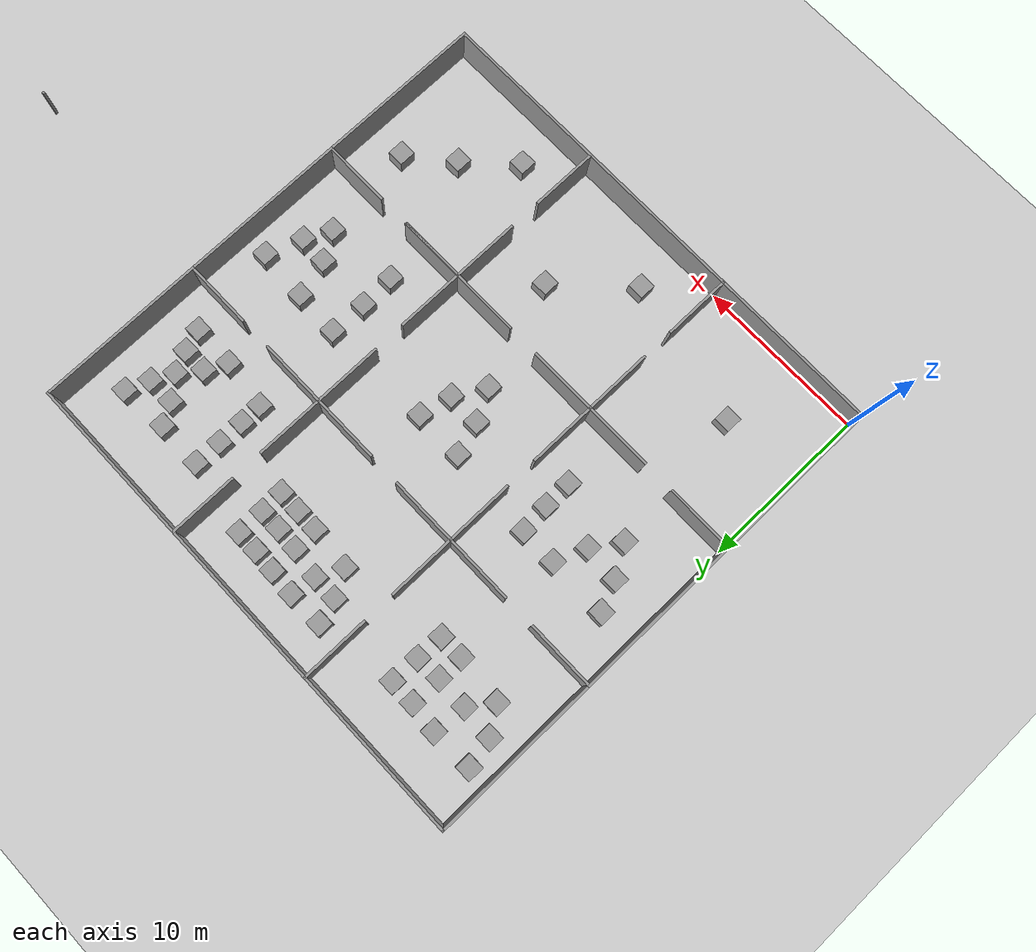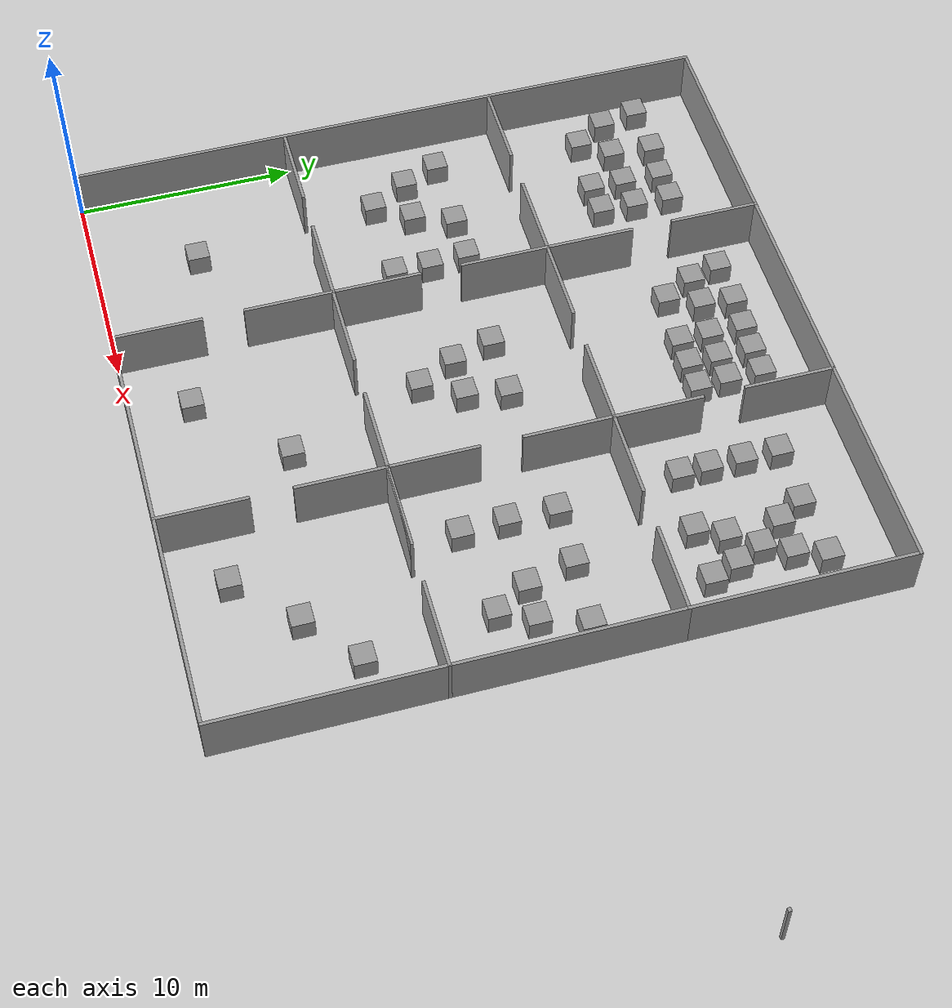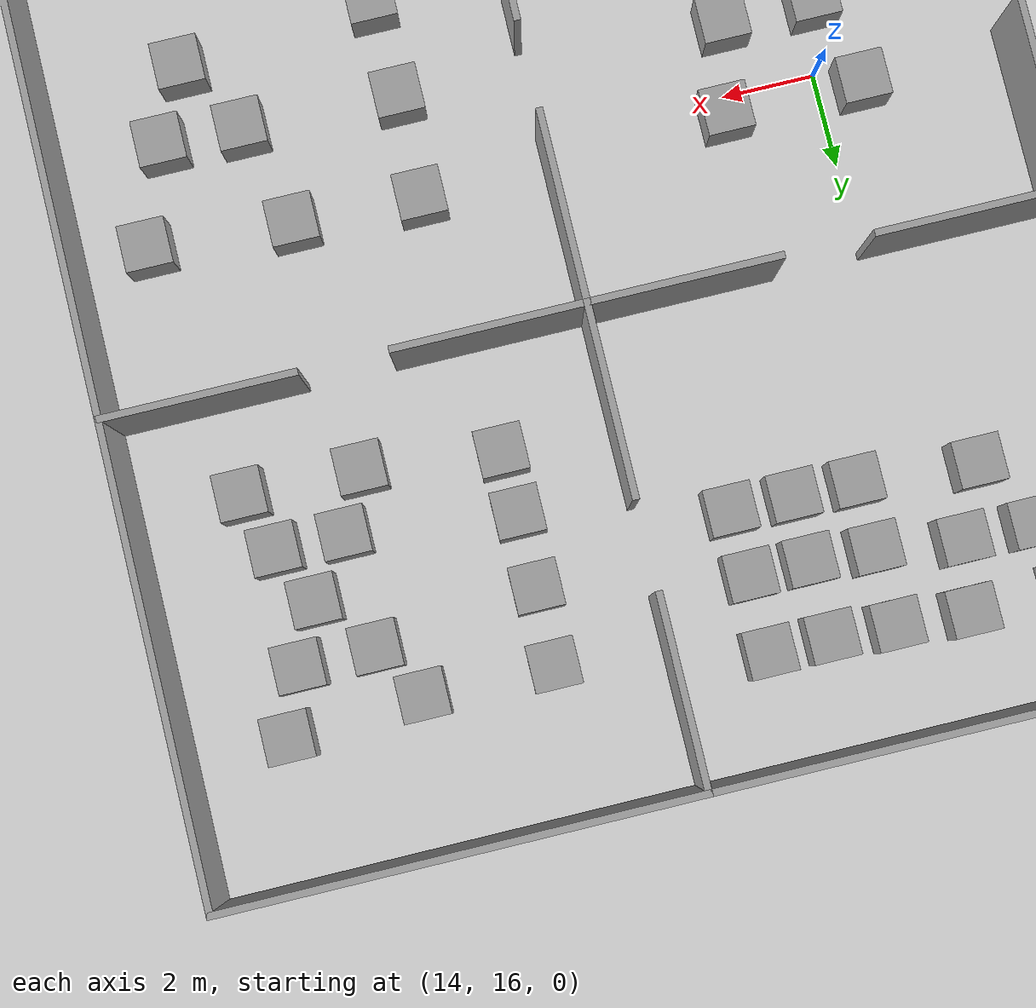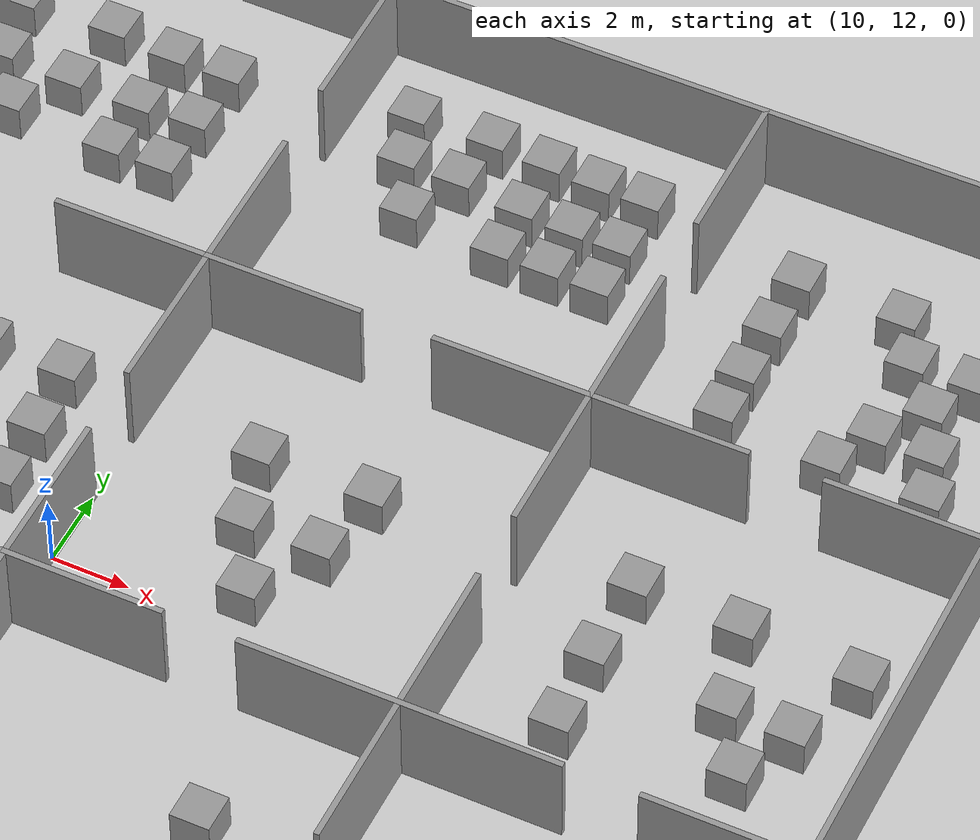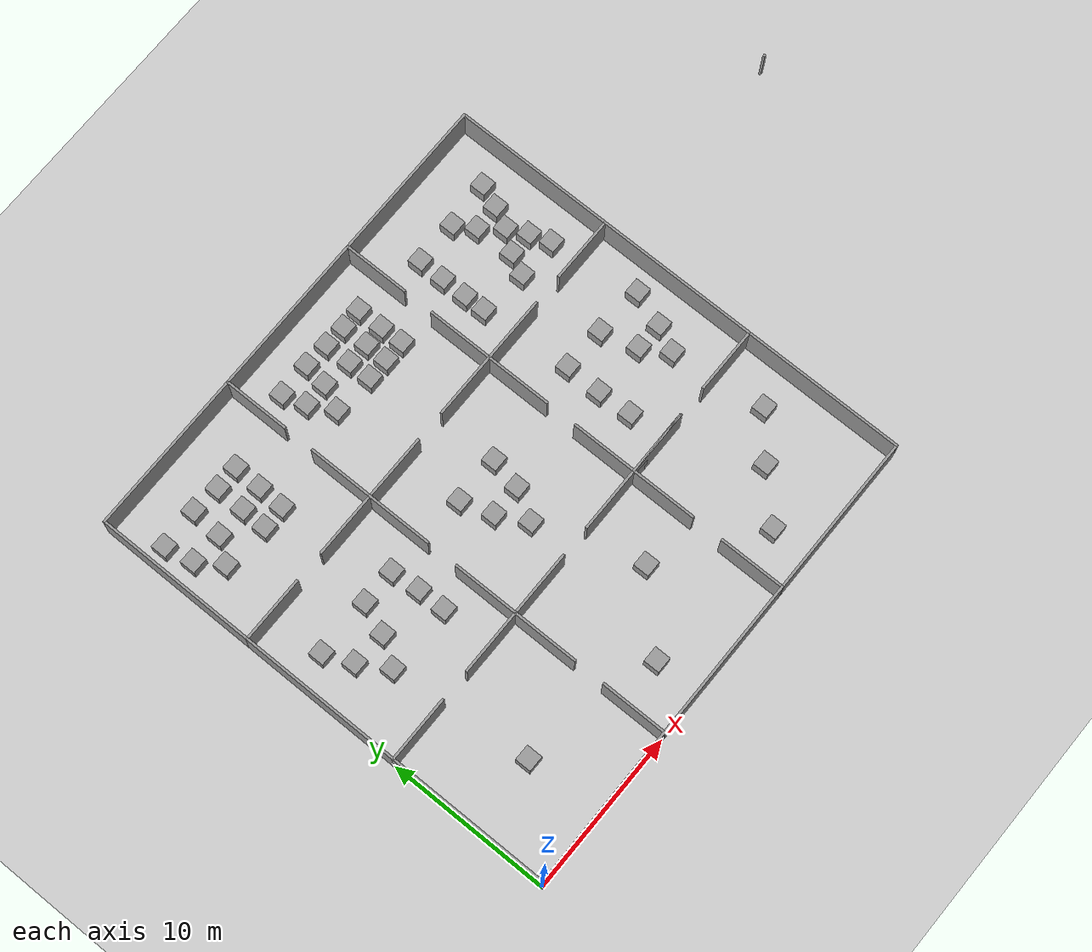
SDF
<sdf version="1.7">
 <world name="default">
  <light name="sun" type="directional">
   <pose>0 0 10 0 -0 0</pose>
   <diffuse>0.8 0.8 0.8 1</diffuse>
   <specular>0.2 0.2 0.2 1</specular>
   <attenuation>
    <range>1000</range>
    <constant>0.9</constant>
    <linear>0.01</linear>
    <quadratic>0.001</quadratic>
   </attenuation>
   <direction>-0.5 0.1 -0.9</direction>
   <spot><inner_angle>0</inner_angle><outer_angle>0</outer_angle><falloff>0</falloff></spot>
  </light>
  <model name="ground_plane">
   <static>1</static>
   <link name="link">
    <collision name="collision">
     <geometry><plane><normal>0 0 1</normal><size>100 100</size></plane></geometry>
     <surface>
      <contact><collide_bitmask>65535</collide_bitmask></contact>
      <friction><ode><mu>100</mu><mu2>50</mu2></ode></friction>
     </surface>
    </collision>
    <visual name="visual">
     <cast_shadows>0</cast_shadows>
     <geometry><plane><normal>0 0 1</normal><size>100 100</size></plane></geometry>
     <material>
      <script><uri>file://media/materials/scripts/gazebo.material</uri><name>Gazebo/Grey</name></script>
     </material>
    </visual>
   </link>
  </model>
  <gravity>0 0 -9.8</gravity>
  <magnetic_field>6e-06 2.3e-05 -4.2e-05</magnetic_field>
  <atmosphere type="adiabatic"/>
  <physics type="ode">
   <max_step_size>0.001</max_step_size>
   <real_time_factor>1</real_time_factor>
   <real_time_update_rate>1000</real_time_update_rate>
  </physics>
  <scene><ambient>0.4 0.4 0.4 1</ambient><background>0.7 0.7 0.7 1</background><shadows>1</shadows></scene>
  <spherical_coordinates>
   <surface_model>EARTH_WGS84</surface_model>
   <latitude_deg>0</latitude_deg>
   <longitude_deg>0</longitude_deg>
   <elevation>0</elevation>
   <heading_deg>0</heading_deg>
  </spherical_coordinates>
  <model name="Building_3x3">
   <pose>21.6715 15 0 0 -0 0</pose>
   <link name="Wall_17">
    <collision name="Wall_17_Collision">
     <geometry><box><size>4.15 0.15 2.5</size></box></geometry>
     <pose>0 0 1.25 0 -0 0</pose>
    </collision>
    <visual name="Wall_17_Visual">
     <pose>0 0 1.25 0 -0 0</pose>
     <geometry><box><size>4.15 0.15 2.5</size></box></geometry>
     <material>
      <script><uri>file://media/materials/scripts/gazebo.material</uri><name>Gazebo/Grey</name></script>
      <ambient>1 1 1 1</ambient>
     </material>
     <meta><layer>0</layer></meta>
    </visual>
    <pose>-13.6715 -5 0 0 -0 0</pose>
   </link>
   <link name="Wall_20">
    <collision name="Wall_20_Collision">
     <geometry><box><size>10.15 0.15 2.5</size></box></geometry>
     <pose>0 0 1.25 0 -0 0</pose>
    </collision>
    <visual name="Wall_20_Visual">
     <pose>0 0 1.25 0 -0 0</pose>
     <geometry><box><size>10.15 0.15 2.5</size></box></geometry>
     <material>
      <script><uri>file://media/materials/scripts/gazebo.material</uri><name>Gazebo/Grey</name></script>
      <ambient>1 1 1 1</ambient>
     </material>
     <meta><layer>0</layer></meta>
    </visual>
    <pose>-21.6715 -10 0 0 -0 1.5708</pose>
   </link>
   <link name="Wall_22">
    <collision name="Wall_22_Collision">
     <geometry><box><size>4.15 0.15 2.5</size></box></geometry>
     <pose>0 0 1.25 0 -0 0</pose>
    </collision>
    <visual name="Wall_22_Visual">
     <pose>0 0 1.25 0 -0 0</pose>
     <geometry><box><size>4.15 0.15 2.5</size></box></geometry>
     <material>
      <script><uri>file://media/materials/scripts/gazebo.material</uri><name>Gazebo/Grey</name></script>
      <ambient>1 1 1 1</ambient>
     </material>
     <meta><layer>0</layer></meta>
    </visual>
    <pose>-19.6715 -5 0 0 -0 0</pose>
   </link>
   <link name="Wall_26">
    <collision name="Wall_26_Collision">
     <geometry><box><size>10.15 0.15 2.5</size></box></geometry>
     <pose>0 0 1.25 0 -0 0</pose>
    </collision>
    <visual name="Wall_26_Visual">
     <pose>0 0 1.25 0 -0 0</pose>
     <geometry><box><size>10.15 0.15 2.5</size></box></geometry>
     <material>
      <script><uri>file://media/materials/scripts/gazebo.material</uri><name>Gazebo/Grey</name></script>
      <ambient>1 1 1 1</ambient>
     </material>
     <meta><layer>0</layer></meta>
    </visual>
    <pose>-16.6715 -15 0 0 -0 0</pose>
   </link>
   <link name="Wall_28">
    <collision name="Wall_28_Collision">
     <geometry><box><size>4.15 0.15 2.5</size></box></geometry>
     <pose>0 0 1.25 0 -0 0</pose>
    </collision>
    <visual name="Wall_28_Visual">
     <pose>0 0 1.25 0 -0 0</pose>
     <geometry><box><size>4.15 0.15 2.5</size></box></geometry>
     <material>
      <script><uri>file://media/materials/scripts/gazebo.material</uri><name>Gazebo/Grey</name></script>
      <ambient>1 1 1 1</ambient>
     </material>
     <meta><layer>0</layer></meta>
    </visual>
    <pose>-11.6715 -7 0 0 -0 1.5708</pose>
   </link>
   <link name="Wall_30">
    <collision name="Wall_30_Collision">
     <geometry><box><size>4.15 0.15 2.5</size></box></geometry>
     <pose>0 0 1.25 0 -0 0</pose>
    </collision>
    <visual name="Wall_30_Visual">
     <pose>0 0 1.25 0 -0 0</pose>
     <geometry><box><size>4.15 0.15 2.5</size></box></geometry>
     <material>
      <script><uri>file://media/materials/scripts/gazebo.material</uri><name>Gazebo/Grey</name></script>
      <ambient>1 1 1 1</ambient>
     </material>
     <meta><layer>0</layer></meta>
    </visual>
    <pose>-11.6715 -13 0 0 -0 1.5708</pose>
   </link>
   <link name="Wall_33">
    <collision name="Wall_33_Collision">
     <geometry><box><size>10.15 0.15 2.5</size></box></geometry>
     <pose>0 0 1.25 0 -0 0</pose>
    </collision>
    <visual name="Wall_33_Visual">
     <pose>0 0 1.25 0 -0 0</pose>
     <geometry><box><size>10.15 0.15 2.5</size></box></geometry>
     <material>
      <script><uri>file://media/materials/scripts/gazebo.material</uri><name>Gazebo/Grey</name></script>
      <ambient>1 1 1 1</ambient>
     </material>
     <meta><layer>0</layer></meta>
    </visual>
    <pose>-6.67153 -15 0 0 -0 0</pose>
   </link>
   <link name="Wall_35">
    <collision name="Wall_35_Collision">
     <geometry><box><size>4.15 0.15 2.5</size></box></geometry>
     <pose>0 0 1.25 0 -0 0</pose>
    </collision>
    <visual name="Wall_35_Visual">
     <pose>0 0 1.25 0 -0 0</pose>
     <geometry><box><size>4.15 0.15 2.5</size></box></geometry>
     <material>
      <script><uri>file://media/materials/scripts/gazebo.material</uri><name>Gazebo/Grey</name></script>
      <ambient>1 1 1 1</ambient>
     </material>
     <meta><layer>0</layer></meta>
    </visual>
    <pose>-1.67153 -13 0 0 -0 -1.5708</pose>
   </link>
   <link name="Wall_37">
    <collision name="Wall_37_Collision">
     <geometry><box><size>4.15 0.15 2.5</size></box></geometry>
     <pose>0 0 1.25 0 -0 0</pose>
    </collision>
    <visual name="Wall_37_Visual">
     <pose>0 0 1.25 0 -0 0</pose>
     <geometry><box><size>4.15 0.15 2.5</size></box></geometry>
     <material>
      <script><uri>file://media/materials/scripts/gazebo.material</uri><name>Gazebo/Grey</name></script>
      <ambient>1 1 1 1</ambient>
     </material>
     <meta><layer>0</layer></meta>
    </visual>
    <pose>-1.67153 -7 0 0 -0 1.5708</pose>
   </link>
   <link name="Wall_39">
    <collision name="Wall_39_Collision">
     <geometry><box><size>4.15 0.15 2.5</size></box></geometry>
     <pose>0 0 1.25 0 -0 0</pose>
    </collision>
    <visual name="Wall_39_Visual">
     <pose>0 0 1.25 0 -0 0</pose>
     <geometry><box><size>4.15 0.15 2.5</size></box></geometry>
     <material>
      <script><uri>file://media/materials/scripts/gazebo.material</uri><name>Gazebo/Grey</name></script>
      <ambient>1 1 1 1</ambient>
     </material>
     <meta><layer>0</layer></meta>
    </visual>
    <pose>-9.67153 -5 0 0 -0 0</pose>
   </link>
   <link name="Wall_41">
    <collision name="Wall_41_Collision">
     <geometry><box><size>8.15 0.15 2.5</size></box></geometry>
     <pose>0 0 1.25 0 -0 0</pose>
    </collision>
    <visual name="Wall_41_Visual">
     <pose>0 0 1.25 0 -0 0</pose>
     <geometry><box><size>8.15 0.15 2.5</size></box></geometry>
     <material>
      <script><uri>file://media/materials/scripts/gazebo.material</uri><name>Gazebo/Grey</name></script>
      <ambient>1 1 1 1</ambient>
     </material>
     <meta><layer>0</layer></meta>
    </visual>
    <pose>-1.67153 -5 0 0 -0 0</pose>
   </link>
   <link name="Wall_44">
    <collision name="Wall_44_Collision">
     <geometry><box><size>10.15 0.15 2.5</size></box></geometry>
     <pose>0 0 1.25 0 -0 0</pose>
    </collision>
    <visual name="Wall_44_Visual">
     <pose>0 0 1.25 0 -0 0</pose>
     <geometry><box><size>10.15 0.15 2.5</size></box></geometry>
     <material>
      <script><uri>file://media/materials/scripts/gazebo.material</uri><name>Gazebo/Grey</name></script>
      <ambient>1 1 1 1</ambient>
     </material>
     <meta><layer>0</layer></meta>
    </visual>
    <pose>3.32847 -15 0 0 -0 0</pose>
   </link>
   <link name="Wall_46">
    <collision name="Wall_46_Collision">
     <geometry><box><size>10.15 0.15 2.5</size></box></geometry>
     <pose>0 0 1.25 0 -0 0</pose>
    </collision>
    <visual name="Wall_46_Visual">
     <pose>0 0 1.25 0 -0 0</pose>
     <geometry><box><size>10.15 0.15 2.5</size></box></geometry>
     <material>
      <script><uri>file://media/materials/scripts/gazebo.material</uri><name>Gazebo/Grey</name></script>
      <ambient>1 1 1 1</ambient>
     </material>
     <meta><layer>0</layer></meta>
    </visual>
    <pose>8.32847 -10 0 0 -0 1.5708</pose>
   </link>
   <link name="Wall_48">
    <collision name="Wall_48_Collision">
     <geometry><box><size>4.15 0.15 2.5</size></box></geometry>
     <pose>0 0 1.25 0 -0 0</pose>
    </collision>
    <visual name="Wall_48_Visual">
     <pose>0 0 1.25 0 -0 0</pose>
     <geometry><box><size>4.15 0.15 2.5</size></box></geometry>
     <material>
      <script><uri>file://media/materials/scripts/gazebo.material</uri><name>Gazebo/Grey</name></script>
      <ambient>1 1 1 1</ambient>
     </material>
     <meta><layer>0</layer></meta>
    </visual>
    <pose>6.32847 -5 0 0 -0 3.14159</pose>
   </link>
   <link name="Wall_50">
    <collision name="Wall_50_Collision">
     <geometry><box><size>0.16 0.15 2.5</size></box></geometry>
     <pose>0 0 1.25 0 -0 0</pose>
    </collision>
    <visual name="Wall_50_Visual">
     <pose>0 0 1.25 0 -0 0</pose>
     <geometry><box><size>0.16 0.15 2.5</size></box></geometry>
     <material>
      <script><uri>file://media/materials/scripts/gazebo.material</uri><name>Gazebo/Grey</name></script>
      <ambient>1 1 1 1</ambient>
     </material>
     <meta><layer>0</layer></meta>
    </visual>
    <pose>21.6665 4.32487 0 0 -0 0</pose>
   </link>
   <link name="Wall_52">
    <collision name="Wall_52_Collision">
     <geometry><box><size>4.15 0.15 2.5</size></box></geometry>
     <pose>0 0 1.25 0 -0 0</pose>
    </collision>
    <visual name="Wall_52_Visual">
     <pose>0 0 1.25 0 -0 0</pose>
     <geometry><box><size>4.15 0.15 2.5</size></box></geometry>
     <material>
      <script><uri>file://media/materials/scripts/gazebo.material</uri><name>Gazebo/Grey</name></script>
      <ambient>1 1 1 1</ambient>
     </material>
     <meta><layer>0</layer></meta>
    </visual>
    <pose>0.328472 -5 0 0 -0 0</pose>
   </link>
   <link name="Wall_54">
    <collision name="Wall_54_Collision">
     <geometry><box><size>20.15 0.15 2.5</size></box></geometry>
     <pose>0 0 1.25 0 -0 0</pose>
    </collision>
    <visual name="Wall_54_Visual">
     <pose>0 0 1.25 0 -0 0</pose>
     <geometry><box><size>20.15 0.15 2.5</size></box></geometry>
     <material>
      <script><uri>file://media/materials/scripts/gazebo.material</uri><name>Gazebo/Grey</name></script>
      <ambient>1 1 1 1</ambient>
     </material>
     <meta><layer>0</layer></meta>
    </visual>
    <pose>-21.6715 -5 0 0 -0 1.5708</pose>
   </link>
   <link name="Wall_56">
    <collision name="Wall_56_Collision">
     <geometry><box><size>10.15 0.15 2.5</size></box></geometry>
     <pose>0 0 1.25 0 -0 0</pose>
    </collision>
    <visual name="Wall_56_Visual">
     <pose>0 0 1.25 0 -0 0</pose>
     <geometry><box><size>10.15 0.15 2.5</size></box></geometry>
     <material>
      <script><uri>file://media/materials/scripts/gazebo.material</uri><name>Gazebo/Grey</name></script>
      <ambient>1 1 1 1</ambient>
     </material>
     <meta><layer>0</layer></meta>
    </visual>
    <pose>-21.6715 10 0 0 -0 1.5708</pose>
   </link>
   <link name="Wall_58">
    <collision name="Wall_58_Collision">
     <geometry><box><size>10.15 0.15 2.5</size></box></geometry>
     <pose>0 0 1.25 0 -0 0</pose>
    </collision>
    <visual name="Wall_58_Visual">
     <pose>0 0 1.25 0 -0 0</pose>
     <geometry><box><size>10.15 0.15 2.5</size></box></geometry>
     <material>
      <script><uri>file://media/materials/scripts/gazebo.material</uri><name>Gazebo/Grey</name></script>
      <ambient>1 1 1 1</ambient>
     </material>
     <meta><layer>0</layer></meta>
    </visual>
    <pose>3.32847 15 0 0 -0 0</pose>
   </link>
   <link name="Wall_60">
    <collision name="Wall_60_Collision">
     <geometry><box><size>10.15 0.15 2.5</size></box></geometry>
     <pose>0 0 1.25 0 -0 0</pose>
    </collision>
    <visual name="Wall_60_Visual">
     <pose>0 0 1.25 0 -0 0</pose>
     <geometry><box><size>10.15 0.15 2.5</size></box></geometry>
     <material>
      <script><uri>file://media/materials/scripts/gazebo.material</uri><name>Gazebo/Grey</name></script>
      <ambient>1 1 1 1</ambient>
     </material>
     <meta><layer>0</layer></meta>
    </visual>
    <pose>-6.67153 15 0 0 -0 0</pose>
   </link>
   <link name="Wall_62">
    <collision name="Wall_62_Collision">
     <geometry><box><size>10.15 0.15 2.5</size></box></geometry>
     <pose>0 0 1.25 0 -0 0</pose>
    </collision>
    <visual name="Wall_62_Visual">
     <pose>0 0 1.25 0 -0 0</pose>
     <geometry><box><size>10.15 0.15 2.5</size></box></geometry>
     <material>
      <script><uri>file://media/materials/scripts/gazebo.material</uri><name>Gazebo/Grey</name></script>
      <ambient>1 1 1 1</ambient>
     </material>
     <meta><layer>0</layer></meta>
    </visual>
    <pose>-16.6715 15 0 0 -0 0</pose>
   </link>
   <link name="Wall_64">
    <collision name="Wall_64_Collision">
     <geometry><box><size>10.15 0.15 2.5</size></box></geometry>
     <pose>0 0 1.25 0 -0 0</pose>
    </collision>
    <visual name="Wall_64_Visual">
     <pose>0 0 1.25 0 -0 0</pose>
     <geometry><box><size>10.15 0.15 2.5</size></box></geometry>
     <material>
      <script><uri>file://media/materials/scripts/gazebo.material</uri><name>Gazebo/Grey</name></script>
      <ambient>1 1 1 1</ambient>
     </material>
     <meta><layer>0</layer></meta>
    </visual>
    <pose>8.32847 10 0 0 -0 -1.5708</pose>
   </link>
   <link name="Wall_66">
    <collision name="Wall_66_Collision">
     <geometry><box><size>10.15 0.15 2.5</size></box></geometry>
     <pose>0 0 1.25 0 -0 0</pose>
    </collision>
    <visual name="Wall_66_Visual">
     <pose>0 0 1.25 0 -0 0</pose>
     <geometry><box><size>10.15 0.15 2.5</size></box></geometry>
     <material>
      <script><uri>file://media/materials/scripts/gazebo.material</uri><name>Gazebo/Grey</name></script>
      <ambient>1 1 1 1</ambient>
     </material>
     <meta><layer>0</layer></meta>
    </visual>
    <pose>8.32847 0 0 0 -0 -1.5708</pose>
   </link>
   <link name="Wall_68">
    <collision name="Wall_68_Collision">
     <geometry><box><size>4.15 0.15 2.5</size></box></geometry>
     <pose>0 0 1.25 0 -0 0</pose>
    </collision>
    <visual name="Wall_68_Visual">
     <pose>0 0 1.25 0 -0 0</pose>
     <geometry><box><size>4.15 0.15 2.5</size></box></geometry>
     <material>
      <script><uri>file://media/materials/scripts/gazebo.material</uri><name>Gazebo/Grey</name></script>
      <ambient>1 1 1 1</ambient>
     </material>
     <meta><layer>0</layer></meta>
    </visual>
    <pose>-19.6715 5 0 0 -0 0</pose>
   </link>
   <link name="Wall_70">
    <collision name="Wall_70_Collision">
     <geometry><box><size>4.15 0.15 2.5</size></box></geometry>
     <pose>0 0 1.25 0 -0 0</pose>
    </collision>
    <visual name="Wall_70_Visual">
     <pose>0 0 1.25 0 -0 0</pose>
     <geometry><box><size>4.15 0.15 2.5</size></box></geometry>
     <material>
      <script><uri>file://media/materials/scripts/gazebo.material</uri><name>Gazebo/Grey</name></script>
      <ambient>1 1 1 1</ambient>
     </material>
     <meta><layer>0</layer></meta>
    </visual>
    <pose>-13.6715 5 0 0 -0 0</pose>
   </link>
   <link name="Wall_72">
    <collision name="Wall_72_Collision">
     <geometry><box><size>4.15 0.15 2.5</size></box></geometry>
     <pose>0 0 1.25 0 -0 0</pose>
    </collision>
    <visual name="Wall_72_Visual">
     <pose>0 0 1.25 0 -0 0</pose>
     <geometry><box><size>4.15 0.15 2.5</size></box></geometry>
     <material>
      <script><uri>file://media/materials/scripts/gazebo.material</uri><name>Gazebo/Grey</name></script>
      <ambient>1 1 1 1</ambient>
     </material>
     <meta><layer>0</layer></meta>
    </visual>
    <pose>-11.6715 3 0 0 -0 -1.5708</pose>
   </link>
   <link name="Wall_74">
    <collision name="Wall_74_Collision">
     <geometry><box><size>4.15 0.15 2.5</size></box></geometry>
     <pose>0 0 1.25 0 -0 0</pose>
    </collision>
    <visual name="Wall_74_Visual">
     <pose>0 0 1.25 0 -0 0</pose>
     <geometry><box><size>4.15 0.15 2.5</size></box></geometry>
     <material>
      <script><uri>file://media/materials/scripts/gazebo.material</uri><name>Gazebo/Grey</name></script>
      <ambient>1 1 1 1</ambient>
     </material>
     <meta><layer>0</layer></meta>
    </visual>
    <pose>-11.6715 -3 0 0 -0 1.5708</pose>
   </link>
   <link name="Wall_76">
    <collision name="Wall_76_Collision">
     <geometry><box><size>4.15 0.15 2.5</size></box></geometry>
     <pose>0 0 1.25 0 -0 0</pose>
    </collision>
    <visual name="Wall_76_Visual">
     <pose>0 0 1.25 0 -0 0</pose>
     <geometry><box><size>4.15 0.15 2.5</size></box></geometry>
     <material>
      <script><uri>file://media/materials/scripts/gazebo.material</uri><name>Gazebo/Grey</name></script>
      <ambient>1 1 1 1</ambient>
     </material>
     <meta><layer>0</layer></meta>
    </visual>
    <pose>-3.67153 5 0 0 -0 3.14159</pose>
   </link>
   <link name="Wall_78">
    <collision name="Wall_78_Collision">
     <geometry><box><size>4.15 0.15 2.5</size></box></geometry>
     <pose>0 0 1.25 0 -0 0</pose>
    </collision>
    <visual name="Wall_78_Visual">
     <pose>0 0 1.25 0 -0 0</pose>
     <geometry><box><size>4.15 0.15 2.5</size></box></geometry>
     <material>
      <script><uri>file://media/materials/scripts/gazebo.material</uri><name>Gazebo/Grey</name></script>
      <ambient>1 1 1 1</ambient>
     </material>
     <meta><layer>0</layer></meta>
    </visual>
    <pose>-9.67153 5 0 0 -0 0</pose>
   </link>
   <link name="Wall_80">
    <collision name="Wall_80_Collision">
     <geometry><box><size>4.15 0.15 2.5</size></box></geometry>
     <pose>0 0 1.25 0 -0 0</pose>
    </collision>
    <visual name="Wall_80_Visual">
     <pose>0 0 1.25 0 -0 0</pose>
     <geometry><box><size>4.15 0.15 2.5</size></box></geometry>
     <material>
      <script><uri>file://media/materials/scripts/gazebo.material</uri><name>Gazebo/Grey</name></script>
      <ambient>1 1 1 1</ambient>
     </material>
     <meta><layer>0</layer></meta>
    </visual>
    <pose>-1.67153 3 0 0 -0 -1.5708</pose>
   </link>
   <link name="Wall_82">
    <collision name="Wall_82_Collision">
     <geometry><box><size>4.15 0.15 2.5</size></box></geometry>
     <pose>0 0 1.25 0 -0 0</pose>
    </collision>
    <visual name="Wall_82_Visual">
     <pose>0 0 1.25 0 -0 0</pose>
     <geometry><box><size>4.15 0.15 2.5</size></box></geometry>
     <material>
      <script><uri>file://media/materials/scripts/gazebo.material</uri><name>Gazebo/Grey</name></script>
      <ambient>1 1 1 1</ambient>
     </material>
     <meta><layer>0</layer></meta>
    </visual>
    <pose>-1.67153 -3 0 0 -0 1.5708</pose>
   </link>
   <link name="Wall_84">
    <collision name="Wall_84_Collision">
     <geometry><box><size>4.15 0.15 2.5</size></box></geometry>
     <pose>0 0 1.25 0 -0 0</pose>
    </collision>
    <visual name="Wall_84_Visual">
     <pose>0 0 1.25 0 -0 0</pose>
     <geometry><box><size>4.15 0.15 2.5</size></box></geometry>
     <material>
      <script><uri>file://media/materials/scripts/gazebo.material</uri><name>Gazebo/Grey</name></script>
      <ambient>1 1 1 1</ambient>
     </material>
     <meta><layer>0</layer></meta>
    </visual>
    <pose>0.328472 5 0 0 -0 0</pose>
   </link>
   <link name="Wall_86">
    <collision name="Wall_86_Collision">
     <geometry><box><size>4.15 0.15 2.5</size></box></geometry>
     <pose>0 0 1.25 0 -0 0</pose>
    </collision>
    <visual name="Wall_86_Visual">
     <pose>0 0 1.25 0 -0 0</pose>
     <geometry><box><size>4.15 0.15 2.5</size></box></geometry>
     <material>
      <script><uri>file://media/materials/scripts/gazebo.material</uri><name>Gazebo/Grey</name></script>
      <ambient>1 1 1 1</ambient>
     </material>
     <meta><layer>0</layer></meta>
    </visual>
    <pose>6.32847 5 0 0 -0 0</pose>
   </link>
   <link name="Wall_88">
    <collision name="Wall_88_Collision">
     <geometry><box><size>4.15 0.15 2.5</size></box></geometry>
     <pose>0 0 1.25 0 -0 0</pose>
    </collision>
    <visual name="Wall_88_Visual">
     <pose>0 0 1.25 0 -0 0</pose>
     <geometry><box><size>4.15 0.15 2.5</size></box></geometry>
     <material>
      <script><uri>file://media/materials/scripts/gazebo.material</uri><name>Gazebo/Grey</name></script>
      <ambient>1 1 1 1</ambient>
     </material>
     <meta><layer>0</layer></meta>
    </visual>
    <pose>-1.67153 13 0 0 -0 -1.5708</pose>
   </link>
   <link name="Wall_90">
    <collision name="Wall_90_Collision">
     <geometry><box><size>4.15 0.15 2.5</size></box></geometry>
     <pose>0 0 1.25 0 -0 0</pose>
    </collision>
    <visual name="Wall_90_Visual">
     <pose>0 0 1.25 0 -0 0</pose>
     <geometry><box><size>4.15 0.15 2.5</size></box></geometry>
     <material>
      <script><uri>file://media/materials/scripts/gazebo.material</uri><name>Gazebo/Grey</name></script>
      <ambient>1 1 1 1</ambient>
     </material>
     <meta><layer>0</layer></meta>
    </visual>
    <pose>-1.67153 7 0 0 -0 1.5708</pose>
   </link>
   <link name="Wall_92">
    <collision name="Wall_92_Collision">
     <geometry><box><size>4.15 0.15 2.5</size></box></geometry>
     <pose>0 0 1.25 0 -0 0</pose>
    </collision>
    <visual name="Wall_92_Visual">
     <pose>0 0 1.25 0 -0 0</pose>
     <geometry><box><size>4.15 0.15 2.5</size></box></geometry>
     <material>
      <script><uri>file://media/materials/scripts/gazebo.material</uri><name>Gazebo/Grey</name></script>
      <ambient>1 1 1 1</ambient>
     </material>
     <meta><layer>0</layer></meta>
    </visual>
    <pose>-11.6715 7 0 0 -0 1.5708</pose>
   </link>
   <link name="Wall_94">
    <collision name="Wall_94_Collision">
     <geometry><box><size>4.15 0.15 2.5</size></box></geometry>
     <pose>0 0 1.25 0 -0 0</pose>
    </collision>
    <visual name="Wall_94_Visual">
     <pose>0 0 1.25 0 -0 0</pose>
     <geometry><box><size>4.15 0.15 2.5</size></box></geometry>
     <material>
      <script><uri>file://media/materials/scripts/gazebo.material</uri><name>Gazebo/Grey</name></script>
      <ambient>1 1 1 1</ambient>
     </material>
     <meta><layer>0</layer></meta>
    </visual>
    <pose>-11.6715 13 0 0 -0 1.5708</pose>
   </link>
   <static>1</static>
  </model>
  <model name="unit_box">
   <pose>4.67216 4.73049 0.499995 -1e-05 0 0</pose>
   <link name="link">
    <inertial>
     <mass>1</mass>
     <inertia>
      <ixx>0.166667</ixx>
      <ixy>0</ixy>
      <ixz>0</ixz>
      <iyy>0.166667</iyy>
      <iyz>0</iyz>
      <izz>0.166667</izz>
     </inertia>
    </inertial>
    <collision name="collision"><geometry><box><size>1 1 1</size></box></geometry></collision>
    <visual name="visual">
     <geometry><box><size>1 1 1</size></box></geometry>
     <material>
      <script><name>Gazebo/Grey</name><uri>file://media/materials/scripts/gazebo.material</uri></script>
     </material>
    </visual>
   </link>
  </model>
  <model name="unit_box_0">
   <pose>13.043 2.79597 0.499995 0 -1e-05 0</pose>
   <link name="link">
    <inertial>
     <mass>1</mass>
     <inertia>
      <ixx>0.166667</ixx>
      <ixy>0</ixy>
      <ixz>0</ixz>
      <iyy>0.166667</iyy>
      <iyz>0</iyz>
      <izz>0.166667</izz>
     </inertia>
    </inertial>
    <collision name="collision"><geometry><box><size>1 1 1</size></box></geometry></collision>
    <visual name="visual">
     <geometry><box><size>1 1 1</size></box></geometry>
     <material>
      <script><name>Gazebo/Grey</name><uri>file://media/materials/scripts/gazebo.material</uri></script>
     </material>
    </visual>
   </link>
  </model>
  <model name="unit_box_1">
   <pose>16.769 6.47067 0.499995 -1e-05 0 0</pose>
   <link name="link">
    <inertial>
     <mass>1</mass>
     <inertia>
      <ixx>0.166667</ixx>
      <ixy>0</ixy>
      <ixz>0</ixz>
      <iyy>0.166667</iyy>
      <iyz>0</iyz>
      <izz>0.166667</izz>
     </inertia>
    </inertial>
    <collision name="collision"><geometry><box><size>1 1 1</size></box></geometry></collision>
    <visual name="visual">
     <geometry><box><size>1 1 1</size></box></geometry>
     <material>
      <script><name>Gazebo/Grey</name><uri>file://media/materials/scripts/gazebo.material</uri></script>
     </material>
    </visual>
   </link>
  </model>
  <model name="unit_box_1_clone">
   <pose>22.6621 2.46352 0.499995 0 -1e-05 0</pose>
   <link name="link">
    <inertial>
     <mass>1</mass>
     <inertia>
      <ixx>0.166667</ixx>
      <ixy>0</ixy>
      <ixz>0</ixz>
      <iyy>0.166667</iyy>
      <iyz>0</iyz>
      <izz>0.166667</izz>
     </inertia>
    </inertial>
    <collision name="collision"><geometry><box><size>1 1 1</size></box></geometry></collision>
    <visual name="visual">
     <geometry><box><size>1 1 1</size></box></geometry>
     <material>
      <script><name>Gazebo/Grey</name><uri>file://media/materials/scripts/gazebo.material</uri></script>
     </material>
    </visual>
   </link>
  </model>
  <model name="unit_box_1_clone_0">
   <pose>25.228 4.96246 0.499995 -1e-05 -0 0</pose>
   <link name="link">
    <inertial>
     <mass>1</mass>
     <inertia>
      <ixx>0.166667</ixx>
      <ixy>0</ixy>
      <ixz>0</ixz>
      <iyy>0.166667</iyy>
      <iyz>0</iyz>
      <izz>0.166667</izz>
     </inertia>
    </inertial>
    <collision name="collision"><geometry><box><size>1 1 1</size></box></geometry></collision>
    <visual name="visual">
     <geometry><box><size>1 1 1</size></box></geometry>
     <material>
      <script><name>Gazebo/Grey</name><uri>file://media/materials/scripts/gazebo.material</uri></script>
     </material>
    </visual>
   </link>
  </model>
  <model name="unit_box_1_clone_1">
   <pose>27.6999 6.98178 0.499995 -1e-05 0 0</pose>
   <link name="link">
    <inertial>
     <mass>1</mass>
     <inertia>
      <ixx>0.166667</ixx>
      <ixy>0</ixy>
      <ixz>0</ixz>
      <iyy>0.166667</iyy>
      <iyz>0</iyz>
      <izz>0.166667</izz>
     </inertia>
    </inertial>
    <collision name="collision"><geometry><box><size>1 1 1</size></box></geometry></collision>
    <visual name="visual">
     <geometry><box><size>1 1 1</size></box></geometry>
     <material>
      <script><name>Gazebo/Grey</name><uri>file://media/materials/scripts/gazebo.material</uri></script>
     </material>
    </visual>
   </link>
  </model>
  <model name="unit_box_2">
   <pose>22.7346 16.6997 0.499995 0 -1e-05 0</pose>
   <link name="link">
    <inertial>
     <mass>1</mass>
     <inertia>
      <ixx>0.166667</ixx>
      <ixy>0</ixy>
      <ixz>0</ixz>
      <iyy>0.166667</iyy>
      <iyz>0</iyz>
      <izz>0.166667</izz>
     </inertia>
    </inertial>
    <collision name="collision"><geometry><box><size>1 1 1</size></box></geometry></collision>
    <visual name="visual">
     <geometry><box><size>1 1 1</size></box></geometry>
     <material>
      <script><name>Gazebo/Grey</name><uri>file://media/materials/scripts/gazebo.material</uri></script>
     </material>
    </visual>
   </link>
  </model>
  <model name="unit_box_1_clone_2">
   <pose>22.6959 14.4762 0.499995 -1e-05 -0 0</pose>
   <link name="link">
    <inertial>
     <mass>1</mass>
     <inertia>
      <ixx>0.166667</ixx>
      <ixy>0</ixy>
      <ixz>0</ixz>
      <iyy>0.166667</iyy>
      <iyz>0</iyz>
      <izz>0.166667</izz>
     </inertia>
    </inertial>
    <collision name="collision"><geometry><box><size>1 1 1</size></box></geometry></collision>
    <visual name="visual">
     <geometry><box><size>1 1 1</size></box></geometry>
     <material>
      <script><name>Gazebo/Grey</name><uri>file://media/materials/scripts/gazebo.material</uri></script>
     </material>
    </visual>
   </link>
  </model>
  <model name="unit_box_1_clone_3">
   <pose>22.7952 12.3886 0.499995 0 -1e-05 0</pose>
   <link name="link">
    <inertial>
     <mass>1</mass>
     <inertia>
      <ixx>0.166667</ixx>
      <ixy>0</ixy>
      <ixz>0</ixz>
      <iyy>0.166667</iyy>
      <iyz>0</iyz>
      <izz>0.166667</izz>
     </inertia>
    </inertial>
    <collision name="collision"><geometry><box><size>1 1 1</size></box></geometry></collision>
    <visual name="visual">
     <geometry><box><size>1 1 1</size></box></geometry>
     <material>
      <script><name>Gazebo/Grey</name><uri>file://media/materials/scripts/gazebo.material</uri></script>
     </material>
    </visual>
   </link>
  </model>
  <model name="unit_box_1_clone_4">
   <pose>25.4457 16.6107 0.499995 -1e-05 0 0</pose>
   <link name="link">
    <inertial>
     <mass>1</mass>
     <inertia>
      <ixx>0.166667</ixx>
      <ixy>0</ixy>
      <ixz>0</ixz>
      <iyy>0.166667</iyy>
      <iyz>0</iyz>
      <izz>0.166667</izz>
     </inertia>
    </inertial>
    <collision name="collision"><geometry><box><size>1 1 1</size></box></geometry></collision>
    <visual name="visual">
     <geometry><box><size>1 1 1</size></box></geometry>
     <material>
      <script><name>Gazebo/Grey</name><uri>file://media/materials/scripts/gazebo.material</uri></script>
     </material>
    </visual>
   </link>
  </model>
  <model name="unit_box_1_clone_5">
   <pose>26.0439 14.3862 0.499995 0 -1e-05 0</pose>
   <link name="link">
    <inertial>
     <mass>1</mass>
     <inertia>
      <ixx>0.166667</ixx>
      <ixy>0</ixy>
      <ixz>0</ixz>
      <iyy>0.166667</iyy>
      <iyz>0</iyz>
      <izz>0.166667</izz>
     </inertia>
    </inertial>
    <collision name="collision"><geometry><box><size>1 1 1</size></box></geometry></collision>
    <visual name="visual">
     <geometry><box><size>1 1 1</size></box></geometry>
     <material>
      <script><name>Gazebo/Grey</name><uri>file://media/materials/scripts/gazebo.material</uri></script>
     </material>
    </visual>
   </link>
  </model>
  <model name="unit_box_1_clone_6">
   <pose>27.0108 12.8015 0.499995 0 -1e-05 0</pose>
   <link name="link">
    <inertial>
     <mass>1</mass>
     <inertia>
      <ixx>0.166667</ixx>
      <ixy>0</ixy>
      <ixz>0</ixz>
      <iyy>0.166667</iyy>
      <iyz>0</iyz>
      <izz>0.166667</izz>
     </inertia>
    </inertial>
    <collision name="collision"><geometry><box><size>1 1 1</size></box></geometry></collision>
    <visual name="visual">
     <geometry><box><size>1 1 1</size></box></geometry>
     <material>
      <script><name>Gazebo/Grey</name><uri>file://media/materials/scripts/gazebo.material</uri></script>
     </material>
    </visual>
   </link>
  </model>
  <model name="unit_box_1_clone_7">
   <pose>27.7529 14.3277 0.499995 0 -1e-05 0</pose>
   <link name="link">
    <inertial>
     <mass>1</mass>
     <inertia>
      <ixx>0.166667</ixx>
      <ixy>0</ixy>
      <ixz>0</ixz>
      <iyy>0.166667</iyy>
      <iyz>0</iyz>
      <izz>0.166667</izz>
     </inertia>
    </inertial>
    <collision name="collision"><geometry><box><size>1 1 1</size></box></geometry></collision>
    <visual name="visual">
     <geometry><box><size>1 1 1</size></box></geometry>
     <material>
      <script><name>Gazebo/Grey</name><uri>file://media/materials/scripts/gazebo.material</uri></script>
     </material>
    </visual>
   </link>
  </model>
  <model name="unit_box_1_clone_8">
   <pose>28.5137 16.4229 0.499995 0 -1e-05 0</pose>
   <link name="link">
    <inertial>
     <mass>1</mass>
     <inertia>
      <ixx>0.166667</ixx>
      <ixy>0</ixy>
      <ixz>0</ixz>
      <iyy>0.166667</iyy>
      <iyz>0</iyz>
      <izz>0.166667</izz>
     </inertia>
    </inertial>
    <collision name="collision"><geometry><box><size>1 1 1</size></box></geometry></collision>
    <visual name="visual">
     <geometry><box><size>1 1 1</size></box></geometry>
     <material>
      <script><name>Gazebo/Grey</name><uri>file://media/materials/scripts/gazebo.material</uri></script>
     </material>
    </visual>
   </link>
  </model>
  <model name="unit_box_1_clone_9">
   <pose>13.1558 16.4643 0.499995 0 -1e-05 0</pose>
   <link name="link">
    <inertial>
     <mass>1</mass>
     <inertia>
      <ixx>0.166667</ixx>
      <ixy>0</ixy>
      <ixz>0</ixz>
      <iyy>0.166667</iyy>
      <iyz>0</iyz>
      <izz>0.166667</izz>
     </inertia>
    </inertial>
    <collision name="collision"><geometry><box><size>1 1 1</size></box></geometry></collision>
    <visual name="visual">
     <geometry><box><size>1 1 1</size></box></geometry>
     <material>
      <script><name>Gazebo/Grey</name><uri>file://media/materials/scripts/gazebo.material</uri></script>
     </material>
    </visual>
   </link>
  </model>
  <model name="unit_box_1_clone_10">
   <pose>16.0976 16.4593 0.499995 -1e-05 -0 0</pose>
   <link name="link">
    <inertial>
     <mass>1</mass>
     <inertia>
      <ixx>0.166667</ixx>
      <ixy>0</ixy>
      <ixz>0</ixz>
      <iyy>0.166667</iyy>
      <iyz>0</iyz>
      <izz>0.166667</izz>
     </inertia>
    </inertial>
    <collision name="collision"><geometry><box><size>1 1 1</size></box></geometry></collision>
    <visual name="visual">
     <geometry><box><size>1 1 1</size></box></geometry>
     <material>
      <script><name>Gazebo/Grey</name><uri>file://media/materials/scripts/gazebo.material</uri></script>
     </material>
    </visual>
   </link>
  </model>
  <model name="unit_box_1_clone_11">
   <pose>13.7413 14.5337 0.499995 0 -1e-05 0</pose>
   <link name="link">
    <inertial>
     <mass>1</mass>
     <inertia>
      <ixx>0.166667</ixx>
      <ixy>0</ixy>
      <ixz>0</ixz>
      <iyy>0.166667</iyy>
      <iyz>0</iyz>
      <izz>0.166667</izz>
     </inertia>
    </inertial>
    <collision name="collision"><geometry><box><size>1 1 1</size></box></geometry></collision>
    <visual name="visual">
     <geometry><box><size>1 1 1</size></box></geometry>
     <material>
      <script><name>Gazebo/Grey</name><uri>file://media/materials/scripts/gazebo.material</uri></script>
     </material>
    </visual>
   </link>
  </model>
  <model name="unit_box_1_clone_12">
   <pose>15.7018 14.5391 0.499995 -1e-05 0 0</pose>
   <link name="link">
    <inertial>
     <mass>1</mass>
     <inertia>
      <ixx>0.166667</ixx>
      <ixy>0</ixy>
      <ixz>0</ixz>
      <iyy>0.166667</iyy>
      <iyz>0</iyz>
      <izz>0.166667</izz>
     </inertia>
    </inertial>
    <collision name="collision"><geometry><box><size>1 1 1</size></box></geometry></collision>
    <visual name="visual">
     <geometry><box><size>1 1 1</size></box></geometry>
     <material>
      <script><name>Gazebo/Grey</name><uri>file://media/materials/scripts/gazebo.material</uri></script>
     </material>
    </visual>
   </link>
  </model>
  <model name="unit_box_1_clone_13">
   <pose>14.6841 12.7445 0.499995 0 -1e-05 0</pose>
   <link name="link">
    <inertial>
     <mass>1</mass>
     <inertia>
      <ixx>0.166667</ixx>
      <ixy>0</ixy>
      <ixz>0</ixz>
      <iyy>0.166667</iyy>
      <iyz>0</iyz>
      <izz>0.166667</izz>
     </inertia>
    </inertial>
    <collision name="collision"><geometry><box><size>1 1 1</size></box></geometry></collision>
    <visual name="visual">
     <geometry><box><size>1 1 1</size></box></geometry>
     <material>
      <script><name>Gazebo/Grey</name><uri>file://media/materials/scripts/gazebo.material</uri></script>
     </material>
    </visual>
   </link>
  </model>
  <model name="unit_box_1_clone_14">
   <pose>2.08488 16.7896 0.499995 -1e-05 -0 0</pose>
   <link name="link">
    <inertial>
     <mass>1</mass>
     <inertia>
      <ixx>0.166667</ixx>
      <ixy>0</ixy>
      <ixz>0</ixz>
      <iyy>0.166667</iyy>
      <iyz>0</iyz>
      <izz>0.166667</izz>
     </inertia>
    </inertial>
    <collision name="collision"><geometry><box><size>1 1 1</size></box></geometry></collision>
    <visual name="visual">
     <geometry><box><size>1 1 1</size></box></geometry>
     <material>
      <script><name>Gazebo/Grey</name><uri>file://media/materials/scripts/gazebo.material</uri></script>
     </material>
    </visual>
   </link>
  </model>
  <model name="unit_box_1_clone_15">
   <pose>2.79814 15.0909 0.499995 -1e-05 -0 0</pose>
   <link name="link">
    <inertial>
     <mass>1</mass>
     <inertia>
      <ixx>0.166667</ixx>
      <ixy>0</ixy>
      <ixz>0</ixz>
      <iyy>0.166667</iyy>
      <iyz>0</iyz>
      <izz>0.166667</izz>
     </inertia>
    </inertial>
    <collision name="collision"><geometry><box><size>1 1 1</size></box></geometry></collision>
    <visual name="visual">
     <geometry><box><size>1 1 1</size></box></geometry>
     <material>
      <script><name>Gazebo/Grey</name><uri>file://media/materials/scripts/gazebo.material</uri></script>
     </material>
    </visual>
   </link>
  </model>
  <model name="unit_box_1_clone_16">
   <pose>3.84151 13.3265 0.499995 -1e-05 -0 0</pose>
   <link name="link">
    <inertial>
     <mass>1</mass>
     <inertia>
      <ixx>0.166667</ixx>
      <ixy>0</ixy>
      <ixz>0</ixz>
      <iyy>0.166667</iyy>
      <iyz>0</iyz>
      <izz>0.166667</izz>
     </inertia>
    </inertial>
    <collision name="collision"><geometry><box><size>1 1 1</size></box></geometry></collision>
    <visual name="visual">
     <geometry><box><size>1 1 1</size></box></geometry>
     <material>
      <script><name>Gazebo/Grey</name><uri>file://media/materials/scripts/gazebo.material</uri></script>
     </material>
    </visual>
   </link>
  </model>
  <model name="unit_box_1_clone_17">
   <pose>4.9272 14.9407 0.499995 0 -1e-05 0</pose>
   <link name="link">
    <inertial>
     <mass>1</mass>
     <inertia>
      <ixx>0.166667</ixx>
      <ixy>0</ixy>
      <ixz>0</ixz>
      <iyy>0.166667</iyy>
      <iyz>0</iyz>
      <izz>0.166667</izz>
     </inertia>
    </inertial>
    <collision name="collision"><geometry><box><size>1 1 1</size></box></geometry></collision>
    <visual name="visual">
     <geometry><box><size>1 1 1</size></box></geometry>
     <material>
      <script><name>Gazebo/Grey</name><uri>file://media/materials/scripts/gazebo.material</uri></script>
     </material>
    </visual>
   </link>
  </model>
  <model name="unit_box_1_clone_18">
   <pose>5.65343 16.785 0.499995 -1e-05 0 0</pose>
   <link name="link">
    <inertial>
     <mass>1</mass>
     <inertia>
      <ixx>0.166667</ixx>
      <ixy>0</ixy>
      <ixz>0</ixz>
      <iyy>0.166667</iyy>
      <iyz>0</iyz>
      <izz>0.166667</izz>
     </inertia>
    </inertial>
    <collision name="collision"><geometry><box><size>1 1 1</size></box></geometry></collision>
    <visual name="visual">
     <geometry><box><size>1 1 1</size></box></geometry>
     <material>
      <script><name>Gazebo/Grey</name><uri>file://media/materials/scripts/gazebo.material</uri></script>
     </material>
    </visual>
   </link>
  </model>
  <model name="unit_box_1_clone_19">
   <pose>7.85351 16.7659 0.499995 0 -1e-05 0</pose>
   <link name="link">
    <inertial>
     <mass>1</mass>
     <inertia>
      <ixx>0.166667</ixx>
      <ixy>0</ixy>
      <ixz>0</ixz>
      <iyy>0.166667</iyy>
      <iyz>0</iyz>
      <izz>0.166667</izz>
     </inertia>
    </inertial>
    <collision name="collision"><geometry><box><size>1 1 1</size></box></geometry></collision>
    <visual name="visual">
     <geometry><box><size>1 1 1</size></box></geometry>
     <material>
      <script><name>Gazebo/Grey</name><uri>file://media/materials/scripts/gazebo.material</uri></script>
     </material>
    </visual>
   </link>
  </model>
  <model name="unit_box_1_clone_20">
   <pose>8 15 0.499995 -1e-05 -0 0</pose>
   <link name="link">
    <inertial>
     <mass>1</mass>
     <inertia>
      <ixx>0.166667</ixx>
      <ixy>0</ixy>
      <ixz>0</ixz>
      <iyy>0.166667</iyy>
      <iyz>0</iyz>
      <izz>0.166667</izz>
     </inertia>
    </inertial>
    <collision name="collision"><geometry><box><size>1 1 1</size></box></geometry></collision>
    <visual name="visual">
     <geometry><box><size>1 1 1</size></box></geometry>
     <material>
      <script><name>Gazebo/Grey</name><uri>file://media/materials/scripts/gazebo.material</uri></script>
     </material>
    </visual>
   </link>
  </model>
  <model name="unit_box_1_clone_21">
   <pose>8.03412 13.2963 0.499995 -1e-05 -0 0</pose>
   <link name="link">
    <inertial>
     <mass>1</mass>
     <inertia>
      <ixx>0.166667</ixx>
      <ixy>0</ixy>
      <ixz>0</ixz>
      <iyy>0.166667</iyy>
      <iyz>0</iyz>
      <izz>0.166667</izz>
     </inertia>
    </inertial>
    <collision name="collision"><geometry><box><size>1 1 1</size></box></geometry></collision>
    <visual name="visual">
     <geometry><box><size>1 1 1</size></box></geometry>
     <material>
      <script><name>Gazebo/Grey</name><uri>file://media/materials/scripts/gazebo.material</uri></script>
     </material>
    </visual>
   </link>
  </model>
  <model name="unit_box_1_clone_22">
   <pose>1.1822 27.0628 0.499995 0 -1e-05 0</pose>
   <link name="link">
    <inertial>
     <mass>1</mass>
     <inertia>
      <ixx>0.166667</ixx>
      <ixy>0</ixy>
      <ixz>0</ixz>
      <iyy>0.166667</iyy>
      <iyz>0</iyz>
      <izz>0.166667</izz>
     </inertia>
    </inertial>
    <collision name="collision"><geometry><box><size>1 1 1</size></box></geometry></collision>
    <visual name="visual">
     <geometry><box><size>1 1 1</size></box></geometry>
     <material>
      <script><name>Gazebo/Grey</name><uri>file://media/materials/scripts/gazebo.material</uri></script>
     </material>
    </visual>
   </link>
  </model>
  <model name="unit_box_1_clone_23">
   <pose>1.52923 25.3163 0.499995 -1e-05 0 0</pose>
   <link name="link">
    <inertial>
     <mass>1</mass>
     <inertia>
      <ixx>0.166667</ixx>
      <ixy>0</ixy>
      <ixz>0</ixz>
      <iyy>0.166667</iyy>
      <iyz>0</iyz>
      <izz>0.166667</izz>
     </inertia>
    </inertial>
    <collision name="collision"><geometry><box><size>1 1 1</size></box></geometry></collision>
    <visual name="visual">
     <geometry><box><size>1 1 1</size></box></geometry>
     <material>
      <script><name>Gazebo/Grey</name><uri>file://media/materials/scripts/gazebo.material</uri></script>
     </material>
    </visual>
   </link>
  </model>
  <model name="unit_box_1_clone_24">
   <pose>2.51056 23.8512 0.499995 0 -1e-05 0</pose>
   <link name="link">
    <inertial>
     <mass>1</mass>
     <inertia>
      <ixx>0.166667</ixx>
      <ixy>0</ixy>
      <ixz>0</ixz>
      <iyy>0.166667</iyy>
      <iyz>0</iyz>
      <izz>0.166667</izz>
     </inertia>
    </inertial>
    <collision name="collision"><geometry><box><size>1 1 1</size></box></geometry></collision>
    <visual name="visual">
     <geometry><box><size>1 1 1</size></box></geometry>
     <material>
      <script><name>Gazebo/Grey</name><uri>file://media/materials/scripts/gazebo.material</uri></script>
     </material>
    </visual>
   </link>
  </model>
  <model name="unit_box_1_clone_25">
   <pose>3.50091 25.185 0.499995 0 -1e-05 0</pose>
   <link name="link">
    <inertial>
     <mass>1</mass>
     <inertia>
      <ixx>0.166667</ixx>
      <ixy>0</ixy>
      <ixz>0</ixz>
      <iyy>0.166667</iyy>
      <iyz>0</iyz>
      <izz>0.166667</izz>
     </inertia>
    </inertial>
    <collision name="collision"><geometry><box><size>1 1 1</size></box></geometry></collision>
    <visual name="visual">
     <geometry><box><size>1 1 1</size></box></geometry>
     <material>
      <script><name>Gazebo/Grey</name><uri>file://media/materials/scripts/gazebo.material</uri></script>
     </material>
    </visual>
   </link>
  </model>
  <model name="unit_box_1_clone_26">
   <pose>3.66779 27.1444 0.499995 0 -1e-05 0</pose>
   <link name="link">
    <inertial>
     <mass>1</mass>
     <inertia>
      <ixx>0.166667</ixx>
      <ixy>0</ixy>
      <ixz>0</ixz>
      <iyy>0.166667</iyy>
      <iyz>0</iyz>
      <izz>0.166667</izz>
     </inertia>
    </inertial>
    <collision name="collision"><geometry><box><size>1 1 1</size></box></geometry></collision>
    <visual name="visual">
     <geometry><box><size>1 1 1</size></box></geometry>
     <material>
      <script><name>Gazebo/Grey</name><uri>file://media/materials/scripts/gazebo.material</uri></script>
     </material>
    </visual>
   </link>
  </model>
  <model name="unit_box_1_clone_27">
   <pose>5.42955 26.9683 0.499995 -1e-05 -0 0</pose>
   <link name="link">
    <inertial>
     <mass>1</mass>
     <inertia>
      <ixx>0.166667</ixx>
      <ixy>0</ixy>
      <ixz>0</ixz>
      <iyy>0.166667</iyy>
      <iyz>0</iyz>
      <izz>0.166667</izz>
     </inertia>
    </inertial>
    <collision name="collision"><geometry><box><size>1 1 1</size></box></geometry></collision>
    <visual name="visual">
     <geometry><box><size>1 1 1</size></box></geometry>
     <material>
      <script><name>Gazebo/Grey</name><uri>file://media/materials/scripts/gazebo.material</uri></script>
     </material>
    </visual>
   </link>
  </model>
  <model name="unit_box_1_clone_28">
   <pose>5.3997 25.152 0.499995 0 -1e-05 0</pose>
   <link name="link">
    <inertial>
     <mass>1</mass>
     <inertia>
      <ixx>0.166667</ixx>
      <ixy>0</ixy>
      <ixz>0</ixz>
      <iyy>0.166667</iyy>
      <iyz>0</iyz>
      <izz>0.166667</izz>
     </inertia>
    </inertial>
    <collision name="collision"><geometry><box><size>1 1 1</size></box></geometry></collision>
    <visual name="visual">
     <geometry><box><size>1 1 1</size></box></geometry>
     <material>
      <script><name>Gazebo/Grey</name><uri>file://media/materials/scripts/gazebo.material</uri></script>
     </material>
    </visual>
   </link>
  </model>
  <model name="unit_box_1_clone_29">
   <pose>5.39116 23.6058 0.499995 0 -1e-05 0</pose>
   <link name="link">
    <inertial>
     <mass>1</mass>
     <inertia>
      <ixx>0.166667</ixx>
      <ixy>0</ixy>
      <ixz>0</ixz>
      <iyy>0.166667</iyy>
      <iyz>0</iyz>
      <izz>0.166667</izz>
     </inertia>
    </inertial>
    <collision name="collision"><geometry><box><size>1 1 1</size></box></geometry></collision>
    <visual name="visual">
     <geometry><box><size>1 1 1</size></box></geometry>
     <material>
      <script><name>Gazebo/Grey</name><uri>file://media/materials/scripts/gazebo.material</uri></script>
     </material>
    </visual>
   </link>
  </model>
  <model name="unit_box_1_clone_30">
   <pose>6.9273 26.9779 0.499995 0 -1e-05 0</pose>
   <link name="link">
    <inertial>
     <mass>1</mass>
     <inertia>
      <ixx>0.166667</ixx>
      <ixy>0</ixy>
      <ixz>0</ixz>
      <iyy>0.166667</iyy>
      <iyz>0</iyz>
      <izz>0.166667</izz>
     </inertia>
    </inertial>
    <collision name="collision"><geometry><box><size>1 1 1</size></box></geometry></collision>
    <visual name="visual">
     <geometry><box><size>1 1 1</size></box></geometry>
     <material>
      <script><name>Gazebo/Grey</name><uri>file://media/materials/scripts/gazebo.material</uri></script>
     </material>
    </visual>
   </link>
  </model>
  <model name="unit_box_1_clone_31">
   <pose>6.89119 25.2526 0.499995 0 -1e-05 0</pose>
   <link name="link">
    <inertial>
     <mass>1</mass>
     <inertia>
      <ixx>0.166667</ixx>
      <ixy>0</ixy>
      <ixz>0</ixz>
      <iyy>0.166667</iyy>
      <iyz>0</iyz>
      <izz>0.166667</izz>
     </inertia>
    </inertial>
    <collision name="collision"><geometry><box><size>1 1 1</size></box></geometry></collision>
    <visual name="visual">
     <geometry><box><size>1 1 1</size></box></geometry>
     <material>
      <script><name>Gazebo/Grey</name><uri>file://media/materials/scripts/gazebo.material</uri></script>
     </material>
    </visual>
   </link>
  </model>
  <model name="unit_box_1_clone_32">
   <pose>6.832 23.6315 0.499995 -1e-05 -0 0</pose>
   <link name="link">
    <inertial>
     <mass>1</mass>
     <inertia>
      <ixx>0.166667</ixx>
      <ixy>0</ixy>
      <ixz>0</ixz>
      <iyy>0.166667</iyy>
      <iyz>0</iyz>
      <izz>0.166667</izz>
     </inertia>
    </inertial>
    <collision name="collision"><geometry><box><size>1 1 1</size></box></geometry></collision>
    <visual name="visual">
     <geometry><box><size>1 1 1</size></box></geometry>
     <material>
      <script><name>Gazebo/Grey</name><uri>file://media/materials/scripts/gazebo.material</uri></script>
     </material>
    </visual>
   </link>
  </model>
  <model name="unit_box_1_clone_33">
   <pose>11.6368 27.7329 0.499995 0 -1e-05 0</pose>
   <link name="link">
    <inertial>
     <mass>1</mass>
     <inertia>
      <ixx>0.166667</ixx>
      <ixy>0</ixy>
      <ixz>0</ixz>
      <iyy>0.166667</iyy>
      <iyz>0</iyz>
      <izz>0.166667</izz>
     </inertia>
    </inertial>
    <collision name="collision"><geometry><box><size>1 1 1</size></box></geometry></collision>
    <visual name="visual">
     <geometry><box><size>1 1 1</size></box></geometry>
     <material>
      <script><name>Gazebo/Grey</name><uri>file://media/materials/scripts/gazebo.material</uri></script>
     </material>
    </visual>
   </link>
  </model>
  <model name="unit_box_1_clone_34">
   <pose>12.0485 26.3197 0.499995 0 -1e-05 0</pose>
   <link name="link">
    <inertial>
     <mass>1</mass>
     <inertia>
      <ixx>0.166667</ixx>
      <ixy>0</ixy>
      <ixz>0</ixz>
      <iyy>0.166667</iyy>
      <iyz>0</iyz>
      <izz>0.166667</izz>
     </inertia>
    </inertial>
    <collision name="collision"><geometry><box><size>1 1 1</size></box></geometry></collision>
    <visual name="visual">
     <geometry><box><size>1 1 1</size></box></geometry>
     <material>
      <script><name>Gazebo/Grey</name><uri>file://media/materials/scripts/gazebo.material</uri></script>
     </material>
    </visual>
   </link>
  </model>
  <model name="unit_box_1_clone_35">
   <pose>12.8539 24.8405 0.499995 0 -1e-05 0</pose>
   <link name="link">
    <inertial>
     <mass>1</mass>
     <inertia>
      <ixx>0.166667</ixx>
      <ixy>0</ixy>
      <ixz>0</ixz>
      <iyy>0.166667</iyy>
      <iyz>0</iyz>
      <izz>0.166667</izz>
     </inertia>
    </inertial>
    <collision name="collision"><geometry><box><size>1 1 1</size></box></geometry></collision>
    <visual name="visual">
     <geometry><box><size>1 1 1</size></box></geometry>
     <material>
      <script><name>Gazebo/Grey</name><uri>file://media/materials/scripts/gazebo.material</uri></script>
     </material>
    </visual>
   </link>
  </model>
  <model name="unit_box_1_clone_36">
   <pose>13.5412 26.3055 0.499995 -1e-05 -0 0</pose>
   <link name="link">
    <inertial>
     <mass>1</mass>
     <inertia>
      <ixx>0.166667</ixx>
      <ixy>0</ixy>
      <ixz>0</ixz>
      <iyy>0.166667</iyy>
      <iyz>0</iyz>
      <izz>0.166667</izz>
     </inertia>
    </inertial>
    <collision name="collision"><geometry><box><size>1 1 1</size></box></geometry></collision>
    <visual name="visual">
     <geometry><box><size>1 1 1</size></box></geometry>
     <material>
      <script><name>Gazebo/Grey</name><uri>file://media/materials/scripts/gazebo.material</uri></script>
     </material>
    </visual>
   </link>
  </model>
  <model name="unit_box_1_clone_37">
   <pose>13.747 27.7773 0.499995 -1e-05 0 0</pose>
   <link name="link">
    <inertial>
     <mass>1</mass>
     <inertia>
      <ixx>0.166667</ixx>
      <ixy>0</ixy>
      <ixz>0</ixz>
      <iyy>0.166667</iyy>
      <iyz>0</iyz>
      <izz>0.166667</izz>
     </inertia>
    </inertial>
    <collision name="collision"><geometry><box><size>1 1 1</size></box></geometry></collision>
    <visual name="visual">
     <geometry><box><size>1 1 1</size></box></geometry>
     <material>
      <script><name>Gazebo/Grey</name><uri>file://media/materials/scripts/gazebo.material</uri></script>
     </material>
    </visual>
   </link>
  </model>
  <model name="unit_box_1_clone_38">
   <pose>15.3133 27.6838 0.499995 -1e-05 0 0</pose>
   <link name="link">
    <inertial>
     <mass>1</mass>
     <inertia>
      <ixx>0.166667</ixx>
      <ixy>0</ixy>
      <ixz>0</ixz>
      <iyy>0.166667</iyy>
      <iyz>0</iyz>
      <izz>0.166667</izz>
     </inertia>
    </inertial>
    <collision name="collision"><geometry><box><size>1 1 1</size></box></geometry></collision>
    <visual name="visual">
     <geometry><box><size>1 1 1</size></box></geometry>
     <material>
      <script><name>Gazebo/Grey</name><uri>file://media/materials/scripts/gazebo.material</uri></script>
     </material>
    </visual>
   </link>
  </model>
  <model name="unit_box_1_clone_39">
   <pose>15.3516 26.0623 0.499995 0 -1e-05 0</pose>
   <link name="link">
    <inertial>
     <mass>1</mass>
     <inertia>
      <ixx>0.166667</ixx>
      <ixy>0</ixy>
      <ixz>0</ixz>
      <iyy>0.166667</iyy>
      <iyz>0</iyz>
      <izz>0.166667</izz>
     </inertia>
    </inertial>
    <collision name="collision"><geometry><box><size>1 1 1</size></box></geometry></collision>
    <visual name="visual">
     <geometry><box><size>1 1 1</size></box></geometry>
     <material>
      <script><name>Gazebo/Grey</name><uri>file://media/materials/scripts/gazebo.material</uri></script>
     </material>
    </visual>
   </link>
  </model>
  <model name="unit_box_1_clone_40">
   <pose>15.3917 24.636 0.499995 -1e-05 0 0</pose>
   <link name="link">
    <inertial>
     <mass>1</mass>
     <inertia>
      <ixx>0.166667</ixx>
      <ixy>0</ixy>
      <ixz>0</ixz>
      <iyy>0.166667</iyy>
      <iyz>0</iyz>
      <izz>0.166667</izz>
     </inertia>
    </inertial>
    <collision name="collision"><geometry><box><size>1 1 1</size></box></geometry></collision>
    <visual name="visual">
     <geometry><box><size>1 1 1</size></box></geometry>
     <material>
      <script><name>Gazebo/Grey</name><uri>file://media/materials/scripts/gazebo.material</uri></script>
     </material>
    </visual>
   </link>
  </model>
  <model name="unit_box_1_clone_41">
   <pose>16.675 27.6092 0.499995 -1e-05 -0 0</pose>
   <link name="link">
    <inertial>
     <mass>1</mass>
     <inertia>
      <ixx>0.166667</ixx>
      <ixy>0</ixy>
      <ixz>0</ixz>
      <iyy>0.166667</iyy>
      <iyz>0</iyz>
      <izz>0.166667</izz>
     </inertia>
    </inertial>
    <collision name="collision"><geometry><box><size>1 1 1</size></box></geometry></collision>
    <visual name="visual">
     <geometry><box><size>1 1 1</size></box></geometry>
     <material>
      <script><name>Gazebo/Grey</name><uri>file://media/materials/scripts/gazebo.material</uri></script>
     </material>
    </visual>
   </link>
  </model>
  <model name="unit_box_1_clone_42">
   <pose>16.7278 25.9912 0.499995 -1e-05 0 0</pose>
   <link name="link">
    <inertial>
     <mass>1</mass>
     <inertia>
      <ixx>0.166667</ixx>
      <ixy>0</ixy>
      <ixz>0</ixz>
      <iyy>0.166667</iyy>
      <iyz>0</iyz>
      <izz>0.166667</izz>
     </inertia>
    </inertial>
    <collision name="collision"><geometry><box><size>1 1 1</size></box></geometry></collision>
    <visual name="visual">
     <geometry><box><size>1 1 1</size></box></geometry>
     <material>
      <script><name>Gazebo/Grey</name><uri>file://media/materials/scripts/gazebo.material</uri></script>
     </material>
    </visual>
   </link>
  </model>
  <model name="unit_box_1_clone_43">
   <pose>16.7281 24.6193 0.499995 0 -1e-05 0</pose>
   <link name="link">
    <inertial>
     <mass>1</mass>
     <inertia>
      <ixx>0.166667</ixx>
      <ixy>0</ixy>
      <ixz>0</ixz>
      <iyy>0.166667</iyy>
      <iyz>0</iyz>
      <izz>0.166667</izz>
     </inertia>
    </inertial>
    <collision name="collision"><geometry><box><size>1 1 1</size></box></geometry></collision>
    <visual name="visual">
     <geometry><box><size>1 1 1</size></box></geometry>
     <material>
      <script><name>Gazebo/Grey</name><uri>file://media/materials/scripts/gazebo.material</uri></script>
     </material>
    </visual>
   </link>
  </model>
  <model name="unit_box_1_clone_44">
   <pose>17.9829 27.6151 0.499995 -1e-05 0 0</pose>
   <link name="link">
    <inertial>
     <mass>1</mass>
     <inertia>
      <ixx>0.166667</ixx>
      <ixy>0</ixy>
      <ixz>0</ixz>
      <iyy>0.166667</iyy>
      <iyz>0</iyz>
      <izz>0.166667</izz>
     </inertia>
    </inertial>
    <collision name="collision"><geometry><box><size>1 1 1</size></box></geometry></collision>
    <visual name="visual">
     <geometry><box><size>1 1 1</size></box></geometry>
     <material>
      <script><name>Gazebo/Grey</name><uri>file://media/materials/scripts/gazebo.material</uri></script>
     </material>
    </visual>
   </link>
  </model>
  <model name="unit_box_1_clone_45">
   <pose>17.9893 26 0.499995 -1e-05 0 0</pose>
   <link name="link">
    <inertial>
     <mass>1</mass>
     <inertia>
      <ixx>0.166667</ixx>
      <ixy>0</ixy>
      <ixz>0</ixz>
      <iyy>0.166667</iyy>
      <iyz>0</iyz>
      <izz>0.166667</izz>
     </inertia>
    </inertial>
    <collision name="collision"><geometry><box><size>1 1 1</size></box></geometry></collision>
    <visual name="visual">
     <geometry><box><size>1 1 1</size></box></geometry>
     <material>
      <script><name>Gazebo/Grey</name><uri>file://media/materials/scripts/gazebo.material</uri></script>
     </material>
    </visual>
   </link>
  </model>
  <model name="unit_box_1_clone_46">
   <pose>18.0507 24.6061 0.499995 0 -1e-05 0</pose>
   <link name="link">
    <inertial>
     <mass>1</mass>
     <inertia>
      <ixx>0.166667</ixx>
      <ixy>0</ixy>
      <ixz>0</ixz>
      <iyy>0.166667</iyy>
      <iyz>0</iyz>
      <izz>0.166667</izz>
     </inertia>
    </inertial>
    <collision name="collision"><geometry><box><size>1 1 1</size></box></geometry></collision>
    <visual name="visual">
     <geometry><box><size>1 1 1</size></box></geometry>
     <material>
      <script><name>Gazebo/Grey</name><uri>file://media/materials/scripts/gazebo.material</uri></script>
     </material>
    </visual>
   </link>
  </model>
  <model name="unit_box_3">
   <pose>27.9358 26.9978 0.499995 0 1e-05 0</pose>
   <link name="link">
    <inertial>
     <mass>1</mass>
     <inertia>
      <ixx>0.166667</ixx>
      <ixy>0</ixy>
      <ixz>0</ixz>
      <iyy>0.166667</iyy>
      <iyz>0</iyz>
      <izz>0.166667</izz>
     </inertia>
    </inertial>
    <collision name="collision"><geometry><box><size>1 1 1</size></box></geometry></collision>
    <visual name="visual">
     <geometry><box><size>1 1 1</size></box></geometry>
     <material>
      <script><name>Gazebo/Grey</name><uri>file://media/materials/scripts/gazebo.material</uri></script>
     </material>
    </visual>
   </link>
  </model>
  <model name="unit_box_3_clone">
   <pose>27.4026 25.6425 0.499995 0 -1e-05 0</pose>
   <link name="link">
    <inertial>
     <mass>1</mass>
     <inertia>
      <ixx>0.166667</ixx>
      <ixy>0</ixy>
      <ixz>0</ixz>
      <iyy>0.166667</iyy>
      <iyz>0</iyz>
      <izz>0.166667</izz>
     </inertia>
    </inertial>
    <collision name="collision"><geometry><box><size>1 1 1</size></box></geometry></collision>
    <visual name="visual">
     <geometry><box><size>1 1 1</size></box></geometry>
     <material>
      <script><name>Gazebo/Grey</name><uri>file://media/materials/scripts/gazebo.material</uri></script>
     </material>
    </visual>
   </link>
  </model>
  <model name="unit_box_3_clone_0">
   <pose>26.7864 24.4124 0.499995 0 -1e-05 0</pose>
   <link name="link">
    <inertial>
     <mass>1</mass>
     <inertia>
      <ixx>0.166667</ixx>
      <ixy>0</ixy>
      <ixz>0</ixz>
      <iyy>0.166667</iyy>
      <iyz>0</iyz>
      <izz>0.166667</izz>
     </inertia>
    </inertial>
    <collision name="collision"><geometry><box><size>1 1 1</size></box></geometry></collision>
    <visual name="visual">
     <geometry><box><size>1 1 1</size></box></geometry>
     <material>
      <script><name>Gazebo/Grey</name><uri>file://media/materials/scripts/gazebo.material</uri></script>
     </material>
    </visual>
   </link>
  </model>
  <model name="unit_box_3_clone_1">
   <pose>25.781 25.6229 0.499995 0 -1e-05 0</pose>
   <link name="link">
    <inertial>
     <mass>1</mass>
     <inertia>
      <ixx>0.166667</ixx>
      <ixy>0</ixy>
      <ixz>0</ixz>
      <iyy>0.166667</iyy>
      <iyz>0</iyz>
      <izz>0.166667</izz>
     </inertia>
    </inertial>
    <collision name="collision"><geometry><box><size>1 1 1</size></box></geometry></collision>
    <visual name="visual">
     <geometry><box><size>1 1 1</size></box></geometry>
     <material>
      <script><name>Gazebo/Grey</name><uri>file://media/materials/scripts/gazebo.material</uri></script>
     </material>
    </visual>
   </link>
  </model>
  <model name="unit_box_3_clone_2">
   <pose>25.0671 26.8091 0.499995 0 -1e-05 0</pose>
   <link name="link">
    <inertial>
     <mass>1</mass>
     <inertia>
      <ixx>0.166667</ixx>
      <ixy>0</ixy>
      <ixz>0</ixz>
      <iyy>0.166667</iyy>
      <iyz>0</iyz>
      <izz>0.166667</izz>
     </inertia>
    </inertial>
    <collision name="collision"><geometry><box><size>1 1 1</size></box></geometry></collision>
    <visual name="visual">
     <geometry><box><size>1 1 1</size></box></geometry>
     <material>
      <script><name>Gazebo/Grey</name><uri>file://media/materials/scripts/gazebo.material</uri></script>
     </material>
    </visual>
   </link>
  </model>
  <model name="unit_box_3_clone_3">
   <pose>27.3466 23.192 0.499995 -1e-05 -0 -0</pose>
   <link name="link">
    <inertial>
     <mass>1</mass>
     <inertia>
      <ixx>0.166667</ixx>
      <ixy>0</ixy>
      <ixz>0</ixz>
      <iyy>0.166667</iyy>
      <iyz>0</iyz>
      <izz>0.166667</izz>
     </inertia>
    </inertial>
    <collision name="collision"><geometry><box><size>1 1 1</size></box></geometry></collision>
    <visual name="visual">
     <geometry><box><size>1 1 1</size></box></geometry>
     <material>
      <script><name>Gazebo/Grey</name><uri>file://media/materials/scripts/gazebo.material</uri></script>
     </material>
    </visual>
   </link>
  </model>
  <model name="unit_box_3_clone_4">
   <pose>25.8764 23.2065 0.499995 0 1e-05 0</pose>
   <link name="link">
    <inertial>
     <mass>1</mass>
     <inertia>
      <ixx>0.166667</ixx>
      <ixy>0</ixy>
      <ixz>0</ixz>
      <iyy>0.166667</iyy>
      <iyz>0</iyz>
      <izz>0.166667</izz>
     </inertia>
    </inertial>
    <collision name="collision"><geometry><box><size>1 1 1</size></box></geometry></collision>
    <visual name="visual">
     <geometry><box><size>1 1 1</size></box></geometry>
     <material>
      <script><name>Gazebo/Grey</name><uri>file://media/materials/scripts/gazebo.material</uri></script>
     </material>
    </visual>
   </link>
  </model>
  <model name="unit_box_3_clone_5">
   <pose>27.7686 21.9319 0.499995 -1e-05 -0 -0</pose>
   <link name="link">
    <inertial>
     <mass>1</mass>
     <inertia>
      <ixx>0.166667</ixx>
      <ixy>0</ixy>
      <ixz>0</ixz>
      <iyy>0.166667</iyy>
      <iyz>0</iyz>
      <izz>0.166667</izz>
     </inertia>
    </inertial>
    <collision name="collision"><geometry><box><size>1 1 1</size></box></geometry></collision>
    <visual name="visual">
     <geometry><box><size>1 1 1</size></box></geometry>
     <material>
      <script><name>Gazebo/Grey</name><uri>file://media/materials/scripts/gazebo.material</uri></script>
     </material>
    </visual>
   </link>
  </model>
  <model name="unit_box_3_clone_6">
   <pose>25.2538 21.9753 0.499995 0 1e-05 0</pose>
   <link name="link">
    <inertial>
     <mass>1</mass>
     <inertia>
      <ixx>0.166667</ixx>
      <ixy>0</ixy>
      <ixz>0</ixz>
      <iyy>0.166667</iyy>
      <iyz>0</iyz>
      <izz>0.166667</izz>
     </inertia>
    </inertial>
    <collision name="collision"><geometry><box><size>1 1 1</size></box></geometry></collision>
    <visual name="visual">
     <geometry><box><size>1 1 1</size></box></geometry>
     <material>
      <script><name>Gazebo/Grey</name><uri>file://media/materials/scripts/gazebo.material</uri></script>
     </material>
    </visual>
   </link>
  </model>
  <model name="unit_box_3_clone_7">
   <pose>22.3266 26.8348 0.499995 0 -1e-05 0</pose>
   <link name="link">
    <inertial>
     <mass>1</mass>
     <inertia>
      <ixx>0.166667</ixx>
      <ixy>0</ixy>
      <ixz>0</ixz>
      <iyy>0.166667</iyy>
      <iyz>0</iyz>
      <izz>0.166667</izz>
     </inertia>
    </inertial>
    <collision name="collision"><geometry><box><size>1 1 1</size></box></geometry></collision>
    <visual name="visual">
     <geometry><box><size>1 1 1</size></box></geometry>
     <material>
      <script><name>Gazebo/Grey</name><uri>file://media/materials/scripts/gazebo.material</uri></script>
     </material>
    </visual>
   </link>
  </model>
  <model name="unit_box_3_clone_8">
   <pose>22.2989 25.2012 0.499995 0 1e-05 0</pose>
   <link name="link">
    <inertial>
     <mass>1</mass>
     <inertia>
      <ixx>0.166667</ixx>
      <ixy>0</ixy>
      <ixz>0</ixz>
      <iyy>0.166667</iyy>
      <iyz>0</iyz>
      <izz>0.166667</izz>
     </inertia>
    </inertial>
    <collision name="collision"><geometry><box><size>1 1 1</size></box></geometry></collision>
    <visual name="visual">
     <geometry><box><size>1 1 1</size></box></geometry>
     <material>
      <script><name>Gazebo/Grey</name><uri>file://media/materials/scripts/gazebo.material</uri></script>
     </material>
    </visual>
   </link>
  </model>
  <model name="unit_box_3_clone_9">
   <pose>22.3111 23.6261 0.499995 -1e-05 -0 0</pose>
   <link name="link">
    <inertial>
     <mass>1</mass>
     <inertia>
      <ixx>0.166667</ixx>
      <ixy>0</ixy>
      <ixz>0</ixz>
      <iyy>0.166667</iyy>
      <iyz>0</iyz>
      <izz>0.166667</izz>
     </inertia>
    </inertial>
    <collision name="collision"><geometry><box><size>1 1 1</size></box></geometry></collision>
    <visual name="visual">
     <geometry><box><size>1 1 1</size></box></geometry>
     <material>
      <script><name>Gazebo/Grey</name><uri>file://media/materials/scripts/gazebo.material</uri></script>
     </material>
    </visual>
   </link>
  </model>
  <model name="unit_box_3_clone_10">
   <pose>22.3449 22.3135 0.5 0 -0 0</pose>
   <link name="link">
    <inertial>
     <mass>1</mass>
     <inertia>
      <ixx>0.166667</ixx>
      <ixy>0</ixy>
      <ixz>0</ixz>
      <iyy>0.166667</iyy>
      <iyz>0</iyz>
      <izz>0.166667</izz>
     </inertia>
    </inertial>
    <collision name="collision"><geometry><box><size>1 1 1</size></box></geometry></collision>
    <visual name="visual">
     <geometry><box><size>1 1 1</size></box></geometry>
     <material>
      <script><name>Gazebo/Grey</name><uri>file://media/materials/scripts/gazebo.material</uri></script>
     </material>
    </visual>
   </link>
  </model>
 </world>
</sdf>
